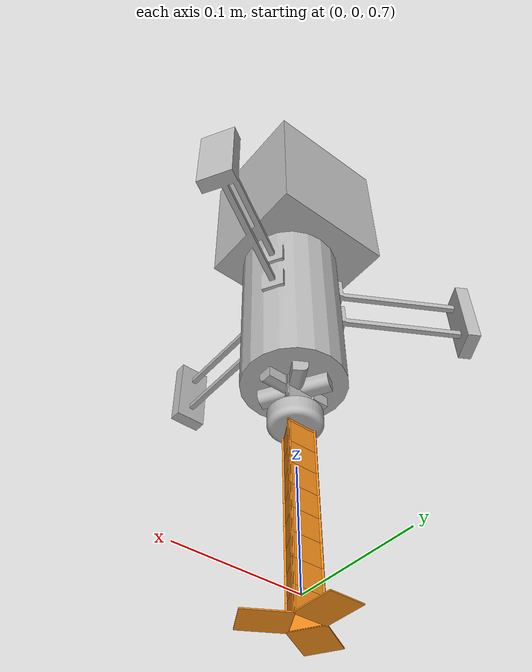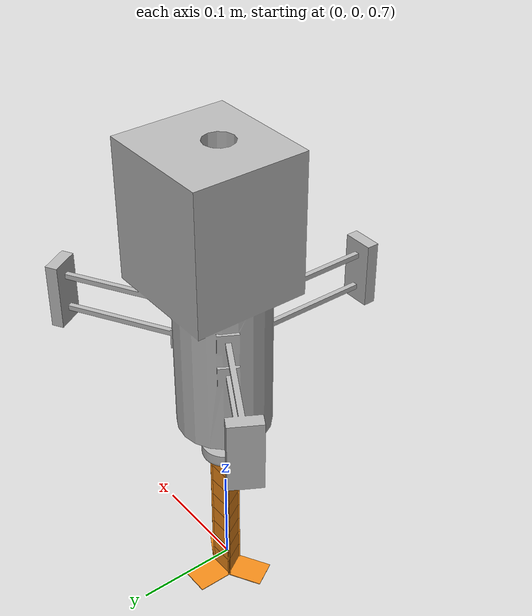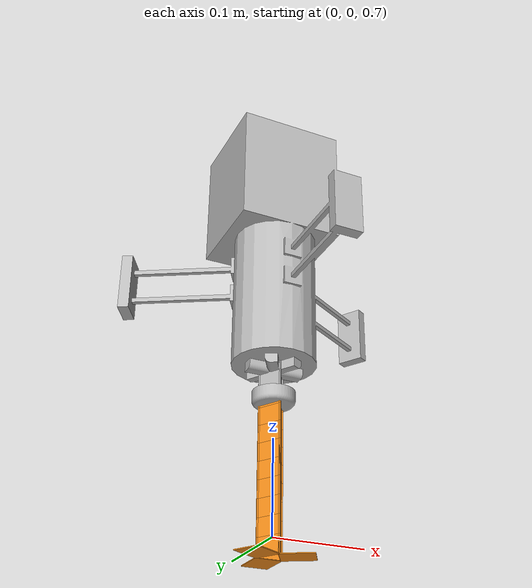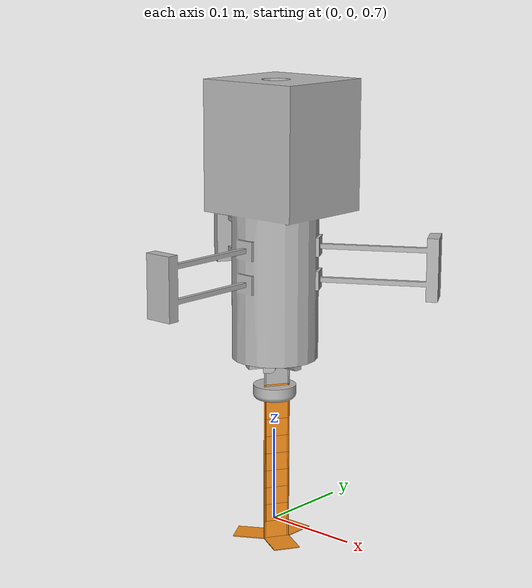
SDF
<sdf version='1.6'>
  <model name='gripper'>
    <link name='gripper_base_link'>
      <pose frame=''>0 0 1 -3.14159 -0 0</pose>
      <inertial>
        <pose frame=''>0 0 0.025 -3.14159 -0 0</pose>
        <mass>1.5</mass>
        <inertia>
          <ixx>0.00995</ixx>
          <ixy>2.73e-06</ixy>
          <ixz>-1.432e-05</ixz>
          <iyy>0.01008</iyy>
          <iyz>0.00012138</iyz>
          <izz>0.00513</izz>
        </inertia>
      </inertial>
      <collision name='gripper_base_link_collision'>
        <pose frame=''>0 0 0 0 -0 0</pose>
        <geometry>
          <mesh>
            <scale>1 1 1</scale>
            <uri>model://gripper_description/meshes/main body collision.STL</uri>
          </mesh>
        </geometry>
      </collision>
      <visual name='gripper_base_link_visual'>
        <pose frame=''>0 0 0 0 -0 0</pose>
        <geometry>
          <mesh>
            <scale>1 1 1</scale>
            <uri>model://gripper_description/meshes/main body visual.STL</uri>
          </mesh>
        </geometry>
      </visual>
    </link>
    <joint name='world_to_base' type='fixed'>
      <child>gripper_base_link</child>
      <parent>world</parent>
    </joint>
    <link name='finger_1_intermediate'>
      <pose frame=''>0 0 1 -3e-06 1.57079 3.14159</pose>
      <inertial>
        <pose frame=''>0 0 0 0 -0 0</pose>
        <mass>0.1</mass>
        <inertia>
          <ixx>5.559e-05</ixx>
          <ixy>-4.723e-05</ixy>
          <ixz>1.16e-06</ixz>
          <iyy>0.00014636</iyy>
          <iyz>1e-06</iyz>
          <izz>0.00015418</izz>
        </inertia>
      </inertial>
      <collision name='finger_1_intermediate_collision'>
        <pose frame=''>0 0 0 0 -0 0</pose>
        <geometry>
          <mesh>
            <scale>1 1 1</scale>
            <uri>model://gripper_description/meshes/nut collision.STL</uri>
          </mesh>
        </geometry>
      </collision>
      <visual name='finger_1_intermediate_visual'>
        <pose frame=''>0 0 0 0 -0 0</pose>
        <geometry>
          <mesh>
            <scale>1 1 1</scale>
            <uri>model://gripper_description/meshes/nut visual.STL</uri>
          </mesh>
        </geometry>
      </visual>
    </link>
    <joint name='finger_1_prismatic_joint' type='prismatic'>
      <child>finger_1_intermediate</child>
      <parent>gripper_base_link</parent>
      <axis>
        <xyz>0 1 0</xyz>
        <limit>
          <lower>0.053</lower>
          <upper>0.141</upper>
          <effort>40</effort>
          <velocity>0.015</velocity>
        </limit>
        <dynamics>
          <damping>1</damping>
          <friction>0</friction>
          <spring_reference>0</spring_reference>
          <spring_stiffness>0</spring_stiffness>
        </dynamics>
        <use_parent_model_frame>0</use_parent_model_frame>
      </axis>
    </joint>
    <link name='finger_1'>
      <pose frame=''>0 0 1 -3e-06 1.57079 3.14159</pose>
      <inertial>
        <pose frame=''>0.007683 -0.000417 0 0 -0 0</pose>
        <mass>0.106333</mass>
        <inertia>
          <ixx>5.62961e-05</ixx>
          <ixy>-4.18516e-05</ixy>
          <ixz>1.16e-06</ixz>
          <iyy>0.000246652</iyy>
          <iyz>1e-06</iyz>
          <izz>0.00025435</izz>
        </inertia>
      </inertial>
      <collision name='finger_1_collision'>
        <pose frame=''>0 0 0 0 -0 0</pose>
        <geometry>
          <mesh>
            <scale>1 1 1</scale>
            <uri>model://gripper_description/meshes/platform only collision.STL</uri>
          </mesh>
        </geometry>
      </collision>
      <collision name='finger_1_segment_link_1_collision_1'>
        <pose frame=''>0.1385 -0.007 0 1.5708 -0 0</pose>
        <geometry>
          <box>
            <size>0.019 0.028 0.0009</size>
          </box>
        </geometry>
      </collision>
      <visual name='finger_1_visual'>
        <pose frame=''>0 0 0 0 -0 0</pose>
        <geometry>
          <mesh>
            <scale>1 1 1</scale>
            <uri>model://gripper_description/meshes/platform only visual.STL</uri>
          </mesh>
        </geometry>
      </visual>
      <visual name='finger_1_segment_link_1_visual_1'>
        <pose frame=''>0.1385 -0.007 0 1.5708 -0 0</pose>
        <geometry>
          <box>
            <size>0.019 0.028 0.0009</size>
          </box>
        </geometry>
      </visual>
      <gravity>1</gravity>
      <velocity_decay/>
    </link>
    <joint name='finger_1_revolute_joint' type='revolute'>
      <child>finger_1</child>
      <parent>finger_1_intermediate</parent>
      <axis>
        <xyz>0 0 1</xyz>
        <limit>
          <lower>-0.7</lower>
          <upper>0.7</upper>
          <effort>40</effort>
          <velocity>0.1</velocity>
        </limit>
        <dynamics>
          <damping>1</damping>
          <friction>0</friction>
          <spring_reference>0</spring_reference>
          <spring_stiffness>0</spring_stiffness>
        </dynamics>
        <use_parent_model_frame>0</use_parent_model_frame>
      </axis>
    </joint>
    <link name='finger_1_segment_link_2'>
      <pose frame=''>-0 0.007 0.852 1.57079 1.57079 3.14159</pose>
      <inertial>
        <pose frame=''>0 0 0 0 -0 0</pose>
        <mass>0.00633333</mass>
        <inertia>
          <ixx>4.14205e-07</ixx>
          <ixy>0</ixy>
          <ixz>0</ixz>
          <iyy>7.62539e-07</iyy>
          <iyz>0</iyz>
          <izz>1.17589e-06</izz>
        </inertia>
      </inertial>
      <collision name='finger_1_segment_link_2_collision'>
        <pose frame=''>0.0095 0 0 0 -0 0</pose>
        <geometry>
          <box>
            <size>0.019 0.028 0.0009</size>
          </box>
        </geometry>
        <surface>
          <contact>
            <ode>
              <max_vel>0</max_vel>
              <min_depth>0.001</min_depth>
            </ode>
          </contact>
          <friction>
            <ode>
              <mu>0.1</mu>
              <mu2>0.1</mu2>
            </ode>
          </friction>
        </surface>
      </collision>
      <visual name='finger_1_segment_link_2_visual'>
        <pose frame=''>0.0095 0 0 0 -0 0</pose>
        <geometry>
          <box>
            <size>0.019 0.028 0.0009</size>
          </box>
        </geometry>
        <material>
          <script>
            <name>Gazebo/Orange</name>
            <uri>file://media/materials/scripts/gazebo.material</uri>
          </script>
        </material>
      </visual>
      <gravity>1</gravity>
      <velocity_decay/>
    </link>
    <joint name='finger_1_segment_joint_1' type='revolute'>
      <child>finger_1_segment_link_2</child>
      <parent>finger_1</parent>
      <axis>
        <xyz>0 1 0</xyz>
        <limit>
          <lower>-1</lower>
          <upper>1</upper>
          <effort>1000</effort>
          <velocity>1</velocity>
        </limit>
        <dynamics>
          <damping>0.001</damping>
          <friction>0</friction>
          <spring_reference>0</spring_reference>
          <spring_stiffness>3</spring_stiffness>
        </dynamics>
        <use_parent_model_frame>0</use_parent_model_frame>
      </axis>
      <physics>
        <provide_feedback>1</provide_feedback>
        <ode>
          <provide_feedback>1</provide_feedback>
          <implicit_spring_damper>1</implicit_spring_damper>
          <cfm_damping>1</cfm_damping>
          <limit>
            <cfm>0</cfm>
            <erp>0.2</erp>
          </limit>
        </ode>
      </physics>
    </joint>
    <link name='finger_1_segment_link_3'>
      <pose frame=''>-0 0.007 0.833 1.57079 1.57079 3.14159</pose>
      <inertial>
        <pose frame=''>0 0 0 0 -0 0</pose>
        <mass>0.00633333</mass>
        <inertia>
          <ixx>4.14205e-07</ixx>
          <ixy>0</ixy>
          <ixz>0</ixz>
          <iyy>7.62539e-07</iyy>
          <iyz>0</iyz>
          <izz>1.17589e-06</izz>
        </inertia>
      </inertial>
      <collision name='finger_1_segment_link_3_collision'>
        <pose frame=''>0.0095 0 0 0 -0 0</pose>
        <geometry>
          <box>
            <size>0.019 0.028 0.0009</size>
          </box>
        </geometry>
        <surface>
          <contact>
            <ode>
              <max_vel>0</max_vel>
              <min_depth>0.001</min_depth>
            </ode>
          </contact>
          <friction>
            <ode>
              <mu>0.1</mu>
              <mu2>0.1</mu2>
            </ode>
          </friction>
        </surface>
      </collision>
      <visual name='finger_1_segment_link_3_visual'>
        <pose frame=''>0.0095 0 0 0 -0 0</pose>
        <geometry>
          <box>
            <size>0.019 0.028 0.0009</size>
          </box>
        </geometry>
        <material>
          <script>
            <name>Gazebo/Orange</name>
            <uri>file://media/materials/scripts/gazebo.material</uri>
          </script>
        </material>
      </visual>
      <gravity>1</gravity>
      <velocity_decay/>
    </link>
    <joint name='finger_1_segment_joint_2' type='revolute'>
      <child>finger_1_segment_link_3</child>
      <parent>finger_1_segment_link_2</parent>
      <axis>
        <xyz>0 1 0</xyz>
        <limit>
          <lower>-1</lower>
          <upper>1</upper>
          <effort>1000</effort>
          <velocity>1</velocity>
        </limit>
        <dynamics>
          <damping>0.001</damping>
          <friction>0</friction>
          <spring_reference>0</spring_reference>
          <spring_stiffness>3</spring_stiffness>
        </dynamics>
        <use_parent_model_frame>0</use_parent_model_frame>
      </axis>
      <physics>
        <provide_feedback>1</provide_feedback>
        <ode>
          <provide_feedback>1</provide_feedback>
          <implicit_spring_damper>1</implicit_spring_damper>
          <cfm_damping>1</cfm_damping>
          <limit>
            <cfm>0</cfm>
            <erp>0.2</erp>
          </limit>
        </ode>
      </physics>
    </joint>
    <link name='finger_1_segment_link_4'>
      <pose frame=''>-0 0.007 0.814 1.57079 1.57079 3.14159</pose>
      <inertial>
        <pose frame=''>0 0 0 0 -0 0</pose>
        <mass>0.00633333</mass>
        <inertia>
          <ixx>4.14205e-07</ixx>
          <ixy>0</ixy>
          <ixz>0</ixz>
          <iyy>7.62539e-07</iyy>
          <iyz>0</iyz>
          <izz>1.17589e-06</izz>
        </inertia>
      </inertial>
      <collision name='finger_1_segment_link_4_collision'>
        <pose frame=''>0.0095 0 0 0 -0 0</pose>
        <geometry>
          <box>
            <size>0.019 0.028 0.0009</size>
          </box>
        </geometry>
        <surface>
          <contact>
            <ode>
              <max_vel>0</max_vel>
              <min_depth>0.001</min_depth>
            </ode>
          </contact>
          <friction>
            <ode>
              <mu>0.1</mu>
              <mu2>0.1</mu2>
            </ode>
          </friction>
        </surface>
      </collision>
      <visual name='finger_1_segment_link_4_visual'>
        <pose frame=''>0.0095 0 0 0 -0 0</pose>
        <geometry>
          <box>
            <size>0.019 0.028 0.0009</size>
          </box>
        </geometry>
        <material>
          <script>
            <name>Gazebo/Orange</name>
            <uri>file://media/materials/scripts/gazebo.material</uri>
          </script>
        </material>
      </visual>
      <gravity>1</gravity>
      <velocity_decay/>
    </link>
    <joint name='finger_1_segment_joint_3' type='revolute'>
      <child>finger_1_segment_link_4</child>
      <parent>finger_1_segment_link_3</parent>
      <axis>
        <xyz>0 1 0</xyz>
        <limit>
          <lower>-1</lower>
          <upper>1</upper>
          <effort>1000</effort>
          <velocity>1</velocity>
        </limit>
        <dynamics>
          <damping>0.001</damping>
          <friction>0</friction>
          <spring_reference>0</spring_reference>
          <spring_stiffness>3</spring_stiffness>
        </dynamics>
        <use_parent_model_frame>0</use_parent_model_frame>
      </axis>
      <physics>
        <provide_feedback>1</provide_feedback>
        <ode>
          <provide_feedback>1</provide_feedback>
          <implicit_spring_damper>1</implicit_spring_damper>
          <cfm_damping>1</cfm_damping>
          <limit>
            <cfm>0</cfm>
            <erp>0.2</erp>
          </limit>
        </ode>
      </physics>
    </joint>
    <link name='finger_1_segment_link_5'>
      <pose frame=''>-0 0.007 0.795 1.57079 1.57079 3.14159</pose>
      <inertial>
        <pose frame=''>0 0 0 0 -0 0</pose>
        <mass>0.00633333</mass>
        <inertia>
          <ixx>4.14205e-07</ixx>
          <ixy>0</ixy>
          <ixz>0</ixz>
          <iyy>7.62539e-07</iyy>
          <iyz>0</iyz>
          <izz>1.17589e-06</izz>
        </inertia>
      </inertial>
      <collision name='finger_1_segment_link_5_collision'>
        <pose frame=''>0.0095 0 0 0 -0 0</pose>
        <geometry>
          <box>
            <size>0.019 0.028 0.0009</size>
          </box>
        </geometry>
        <surface>
          <contact>
            <ode>
              <max_vel>0</max_vel>
              <min_depth>0.001</min_depth>
            </ode>
          </contact>
          <friction>
            <ode>
              <mu>0.1</mu>
              <mu2>0.1</mu2>
            </ode>
          </friction>
        </surface>
      </collision>
      <visual name='finger_1_segment_link_5_visual'>
        <pose frame=''>0.0095 0 0 0 -0 0</pose>
        <geometry>
          <box>
            <size>0.019 0.028 0.0009</size>
          </box>
        </geometry>
        <material>
          <script>
            <name>Gazebo/Orange</name>
            <uri>file://media/materials/scripts/gazebo.material</uri>
          </script>
        </material>
      </visual>
      <gravity>1</gravity>
      <velocity_decay/>
    </link>
    <joint name='finger_1_segment_joint_4' type='revolute'>
      <child>finger_1_segment_link_5</child>
      <parent>finger_1_segment_link_4</parent>
      <axis>
        <xyz>0 1 0</xyz>
        <limit>
          <lower>-1</lower>
          <upper>1</upper>
          <effort>1000</effort>
          <velocity>1</velocity>
        </limit>
        <dynamics>
          <damping>0.001</damping>
          <friction>0</friction>
          <spring_reference>0</spring_reference>
          <spring_stiffness>3</spring_stiffness>
        </dynamics>
        <use_parent_model_frame>0</use_parent_model_frame>
      </axis>
      <physics>
        <provide_feedback>1</provide_feedback>
        <ode>
          <provide_feedback>1</provide_feedback>
          <implicit_spring_damper>1</implicit_spring_damper>
          <cfm_damping>1</cfm_damping>
          <limit>
            <cfm>0</cfm>
            <erp>0.2</erp>
          </limit>
        </ode>
      </physics>
    </joint>
    <link name='finger_1_segment_link_6'>
      <pose frame=''>-0 0.007 0.776 1.57079 1.57079 3.14159</pose>
      <inertial>
        <pose frame=''>0 0 0 0 -0 0</pose>
        <mass>0.00633333</mass>
        <inertia>
          <ixx>4.14205e-07</ixx>
          <ixy>0</ixy>
          <ixz>0</ixz>
          <iyy>7.62539e-07</iyy>
          <iyz>0</iyz>
          <izz>1.17589e-06</izz>
        </inertia>
      </inertial>
      <collision name='finger_1_segment_link_6_collision'>
        <pose frame=''>0.0095 0 0 0 -0 0</pose>
        <geometry>
          <box>
            <size>0.019 0.028 0.0009</size>
          </box>
        </geometry>
        <surface>
          <contact>
            <ode>
              <max_vel>0</max_vel>
              <min_depth>0.001</min_depth>
            </ode>
          </contact>
          <friction>
            <ode>
              <mu>0.1</mu>
              <mu2>0.1</mu2>
            </ode>
          </friction>
        </surface>
      </collision>
      <visual name='finger_1_segment_link_6_visual'>
        <pose frame=''>0.0095 0 0 0 -0 0</pose>
        <geometry>
          <box>
            <size>0.019 0.028 0.0009</size>
          </box>
        </geometry>
        <material>
          <script>
            <name>Gazebo/Orange</name>
            <uri>file://media/materials/scripts/gazebo.material</uri>
          </script>
        </material>
      </visual>
      <gravity>1</gravity>
      <velocity_decay/>
    </link>
    <joint name='finger_1_segment_joint_5' type='revolute'>
      <child>finger_1_segment_link_6</child>
      <parent>finger_1_segment_link_5</parent>
      <axis>
        <xyz>0 1 0</xyz>
        <limit>
          <lower>-1</lower>
          <upper>1</upper>
          <effort>1000</effort>
          <velocity>1</velocity>
        </limit>
        <dynamics>
          <damping>0.001</damping>
          <friction>0</friction>
          <spring_reference>0</spring_reference>
          <spring_stiffness>3</spring_stiffness>
        </dynamics>
        <use_parent_model_frame>0</use_parent_model_frame>
      </axis>
      <physics>
        <provide_feedback>1</provide_feedback>
        <ode>
          <provide_feedback>1</provide_feedback>
          <implicit_spring_damper>1</implicit_spring_damper>
          <cfm_damping>1</cfm_damping>
          <limit>
            <cfm>0</cfm>
            <erp>0.2</erp>
          </limit>
        </ode>
      </physics>
    </joint>
    <link name='finger_1_segment_link_7'>
      <pose frame=''>-0 0.007 0.757 1.57079 1.57079 3.14159</pose>
      <inertial>
        <pose frame=''>0 0 0 0 -0 0</pose>
        <mass>0.00633333</mass>
        <inertia>
          <ixx>4.14205e-07</ixx>
          <ixy>0</ixy>
          <ixz>0</ixz>
          <iyy>7.62539e-07</iyy>
          <iyz>0</iyz>
          <izz>1.17589e-06</izz>
        </inertia>
      </inertial>
      <collision name='finger_1_segment_link_7_collision'>
        <pose frame=''>0.0095 0 0 0 -0 0</pose>
        <geometry>
          <box>
            <size>0.019 0.028 0.0009</size>
          </box>
        </geometry>
        <surface>
          <contact>
            <ode>
              <max_vel>0</max_vel>
              <min_depth>0.001</min_depth>
            </ode>
          </contact>
          <friction>
            <ode>
              <mu>0.1</mu>
              <mu2>0.1</mu2>
            </ode>
          </friction>
        </surface>
      </collision>
      <visual name='finger_1_segment_link_7_visual'>
        <pose frame=''>0.0095 0 0 0 -0 0</pose>
        <geometry>
          <box>
            <size>0.019 0.028 0.0009</size>
          </box>
        </geometry>
        <material>
          <script>
            <name>Gazebo/Orange</name>
            <uri>file://media/materials/scripts/gazebo.material</uri>
          </script>
        </material>
      </visual>
      <gravity>1</gravity>
      <velocity_decay/>
    </link>
    <joint name='finger_1_segment_joint_6' type='revolute'>
      <child>finger_1_segment_link_7</child>
      <parent>finger_1_segment_link_6</parent>
      <axis>
        <xyz>0 1 0</xyz>
        <limit>
          <lower>-1</lower>
          <upper>1</upper>
          <effort>1000</effort>
          <velocity>1</velocity>
        </limit>
        <dynamics>
          <damping>0.001</damping>
          <friction>0</friction>
          <spring_reference>0</spring_reference>
          <spring_stiffness>3</spring_stiffness>
        </dynamics>
        <use_parent_model_frame>0</use_parent_model_frame>
      </axis>
      <physics>
        <provide_feedback>1</provide_feedback>
        <ode>
          <provide_feedback>1</provide_feedback>
          <implicit_spring_damper>1</implicit_spring_damper>
          <cfm_damping>1</cfm_damping>
          <limit>
            <cfm>0</cfm>
            <erp>0.2</erp>
          </limit>
        </ode>
      </physics>
    </joint>
    <link name='finger_1_segment_link_8'>
      <pose frame=''>-0 0.007 0.738 1.57079 1.57079 3.14159</pose>
      <inertial>
        <pose frame=''>0 0 0 0 -0 0</pose>
        <mass>0.00633333</mass>
        <inertia>
          <ixx>4.14205e-07</ixx>
          <ixy>0</ixy>
          <ixz>0</ixz>
          <iyy>7.62539e-07</iyy>
          <iyz>0</iyz>
          <izz>1.17589e-06</izz>
        </inertia>
      </inertial>
      <collision name='finger_1_segment_link_8_collision'>
        <pose frame=''>0.0095 0 0 0 -0 0</pose>
        <geometry>
          <box>
            <size>0.019 0.028 0.0009</size>
          </box>
        </geometry>
        <surface>
          <contact>
            <ode>
              <max_vel>0</max_vel>
              <min_depth>0.001</min_depth>
            </ode>
          </contact>
          <friction>
            <ode>
              <mu>0.1</mu>
              <mu2>0.1</mu2>
            </ode>
          </friction>
        </surface>
      </collision>
      <visual name='finger_1_segment_link_8_visual'>
        <pose frame=''>0.0095 0 0 0 -0 0</pose>
        <geometry>
          <box>
            <size>0.019 0.028 0.0009</size>
          </box>
        </geometry>
        <material>
          <script>
            <name>Gazebo/Orange</name>
            <uri>file://media/materials/scripts/gazebo.material</uri>
          </script>
        </material>
      </visual>
      <gravity>1</gravity>
      <velocity_decay/>
    </link>
    <joint name='finger_1_segment_joint_7' type='revolute'>
      <child>finger_1_segment_link_8</child>
      <parent>finger_1_segment_link_7</parent>
      <axis>
        <xyz>0 1 0</xyz>
        <limit>
          <lower>-1</lower>
          <upper>1</upper>
          <effort>1000</effort>
          <velocity>1</velocity>
        </limit>
        <dynamics>
          <damping>0.001</damping>
          <friction>0</friction>
          <spring_reference>0</spring_reference>
          <spring_stiffness>3</spring_stiffness>
        </dynamics>
        <use_parent_model_frame>0</use_parent_model_frame>
      </axis>
      <physics>
        <provide_feedback>1</provide_feedback>
        <ode>
          <provide_feedback>1</provide_feedback>
          <implicit_spring_damper>1</implicit_spring_damper>
          <cfm_damping>1</cfm_damping>
          <limit>
            <cfm>0</cfm>
            <erp>0.2</erp>
          </limit>
        </ode>
      </physics>
    </joint>
    <link name='finger_1_segment_link_9'>
      <pose frame=''>-0 0.007 0.719 1.57079 1.57079 3.14159</pose>
      <inertial>
        <pose frame=''>0 0 0 0 -0 0</pose>
        <mass>0.00633333</mass>
        <inertia>
          <ixx>4.14205e-07</ixx>
          <ixy>0</ixy>
          <ixz>0</ixz>
          <iyy>7.62539e-07</iyy>
          <iyz>0</iyz>
          <izz>1.17589e-06</izz>
        </inertia>
      </inertial>
      <collision name='finger_1_segment_link_9_collision'>
        <pose frame=''>0.0095 0 0 0 -0 0</pose>
        <geometry>
          <box>
            <size>0.019 0.028 0.0009</size>
          </box>
        </geometry>
        <surface>
          <contact>
            <ode>
              <max_vel>0</max_vel>
              <min_depth>0.001</min_depth>
            </ode>
          </contact>
          <friction>
            <ode>
              <mu>0.1</mu>
              <mu2>0.1</mu2>
            </ode>
          </friction>
        </surface>
      </collision>
      <visual name='finger_1_segment_link_9_visual'>
        <pose frame=''>0.0095 0 0 0 -0 0</pose>
        <geometry>
          <box>
            <size>0.019 0.028 0.0009</size>
          </box>
        </geometry>
        <material>
          <script>
            <name>Gazebo/Orange</name>
            <uri>file://media/materials/scripts/gazebo.material</uri>
          </script>
        </material>
      </visual>
      <gravity>1</gravity>
      <velocity_decay/>
    </link>
    <joint name='finger_1_segment_joint_8' type='revolute'>
      <child>finger_1_segment_link_9</child>
      <parent>finger_1_segment_link_8</parent>
      <axis>
        <xyz>0 1 0</xyz>
        <limit>
          <lower>-1</lower>
          <upper>1</upper>
          <effort>1000</effort>
          <velocity>1</velocity>
        </limit>
        <dynamics>
          <damping>0.001</damping>
          <friction>0</friction>
          <spring_reference>0</spring_reference>
          <spring_stiffness>3</spring_stiffness>
        </dynamics>
        <use_parent_model_frame>0</use_parent_model_frame>
      </axis>
      <physics>
        <provide_feedback>1</provide_feedback>
        <ode>
          <provide_feedback>1</provide_feedback>
          <implicit_spring_damper>1</implicit_spring_damper>
          <cfm_damping>1</cfm_damping>
          <limit>
            <cfm>0</cfm>
            <erp>0.2</erp>
          </limit>
        </ode>
      </physics>
    </joint>
    <link name='finger_1_segment_link_10'>
      <pose frame=''>-0 0.007 0.7 1.57079 1.57079 3.14159</pose>
      <inertial>
        <pose frame=''>0.0095 0 0 0 -0 0</pose>
        <mass>0.0126667</mass>
        <inertia>
          <ixx>1.59009e-06</ixx>
          <ixy>0</ixy>
          <ixz>-4.66397e-23</ixz>
          <iyy>2.66824e-06</iyy>
          <iyz>0</iyz>
          <izz>2.73326e-06</izz>
        </inertia>
      </inertial>
      <collision name='finger_1_segment_link_10_collision'>
        <pose frame=''>0.0095 0 0 0 -0 0</pose>
        <geometry>
          <box>
            <size>0.019 0.028 0.0009</size>
          </box>
        </geometry>
        <surface>
          <contact>
            <ode>
              <max_vel>0</max_vel>
              <min_depth>0.001</min_depth>
            </ode>
          </contact>
          <friction>
            <ode>
              <mu>0.1</mu>
              <mu2>0.1</mu2>
            </ode>
          </friction>
        </surface>
      </collision>
      <collision name='finger_1_segment_link_10_fixed_joint_lump__finger_1_finger_hook_link_collision_1'>
        <pose frame=''>0.019 0 0.0175 3.14159 -1.57079 3.14159</pose>
        <geometry>
          <box>
            <size>0.035 0.028 0.0009</size>
          </box>
        </geometry>
        <surface>
          <contact>
            <ode>
              <max_vel>0</max_vel>
              <min_depth>0.001</min_depth>
            </ode>
          </contact>
          <friction>
            <ode>
              <mu>0.1</mu>
              <mu2>0.1</mu2>
            </ode>
          </friction>
        </surface>
      </collision>
      <visual name='finger_1_segment_link_10_visual'>
        <pose frame=''>0.0095 0 0 0 -0 0</pose>
        <geometry>
          <box>
            <size>0.019 0.028 0.0009</size>
          </box>
        </geometry>
        <material>
          <script>
            <name>Gazebo/Orange</name>
            <uri>file://media/materials/scripts/gazebo.material</uri>
          </script>
        </material>
      </visual>
      <visual name='finger_1_segment_link_10_fixed_joint_lump__finger_1_finger_hook_link_visual_1'>
        <pose frame=''>0.019 0 0.0175 3.14159 -1.57079 3.14159</pose>
        <geometry>
          <box>
            <size>0.035 0.028 0.0009</size>
          </box>
        </geometry>
        <material>
          <script>
            <name>Gazebo/Orange</name>
            <uri>file://media/materials/scripts/gazebo.material</uri>
          </script>
        </material>
      </visual>
      <velocity_decay/>
      <gravity>1</gravity>
      <velocity_decay/>
    </link>
    <joint name='finger_1_segment_joint_9' type='revolute'>
      <child>finger_1_segment_link_10</child>
      <parent>finger_1_segment_link_9</parent>
      <axis>
        <xyz>0 1 0</xyz>
        <limit>
          <lower>-1</lower>
          <upper>1</upper>
          <effort>1000</effort>
          <velocity>1</velocity>
        </limit>
        <dynamics>
          <damping>0.001</damping>
          <friction>0</friction>
          <spring_reference>0</spring_reference>
          <spring_stiffness>3</spring_stiffness>
        </dynamics>
        <use_parent_model_frame>0</use_parent_model_frame>
      </axis>
      <physics>
        <provide_feedback>1</provide_feedback>
        <ode>
          <provide_feedback>1</provide_feedback>
          <implicit_spring_damper>1</implicit_spring_damper>
          <cfm_damping>1</cfm_damping>
          <limit>
            <cfm>0</cfm>
            <erp>0.2</erp>
          </limit>
        </ode>
      </physics>
    </joint>
    <link name='finger_2_intermediate'>
      <pose frame=''>0 0 1 -2.09439 1.57079 3.14159</pose>
      <inertial>
        <pose frame=''>0 0 0 0 -0 0</pose>
        <mass>0.1</mass>
        <inertia>
          <ixx>5.559e-05</ixx>
          <ixy>-4.723e-05</ixy>
          <ixz>1.16e-06</ixz>
          <iyy>0.00014636</iyy>
          <iyz>1e-06</iyz>
          <izz>0.00015418</izz>
        </inertia>
      </inertial>
      <collision name='finger_2_intermediate_collision'>
        <pose frame=''>0 0 0 0 -0 0</pose>
        <geometry>
          <mesh>
            <scale>1 1 1</scale>
            <uri>model://gripper_description/meshes/nut collision.STL</uri>
          </mesh>
        </geometry>
      </collision>
      <visual name='finger_2_intermediate_visual'>
        <pose frame=''>0 0 0 0 -0 0</pose>
        <geometry>
          <mesh>
            <scale>1 1 1</scale>
            <uri>model://gripper_description/meshes/nut visual.STL</uri>
          </mesh>
        </geometry>
      </visual>
    </link>
    <joint name='finger_2_prismatic_joint' type='prismatic'>
      <child>finger_2_intermediate</child>
      <parent>gripper_base_link</parent>
      <axis>
        <xyz>0 1 0</xyz>
        <limit>
          <lower>0.053</lower>
          <upper>0.141</upper>
          <effort>40</effort>
          <velocity>0.015</velocity>
        </limit>
        <dynamics>
          <damping>1</damping>
          <friction>0</friction>
          <spring_reference>0</spring_reference>
          <spring_stiffness>0</spring_stiffness>
        </dynamics>
        <use_parent_model_frame>0</use_parent_model_frame>
      </axis>
    </joint>
    <link name='finger_2'>
      <pose frame=''>0 0 1 -2.09439 1.57079 3.14159</pose>
      <inertial>
        <pose frame=''>0.007683 -0.000417 0 0 -0 0</pose>
        <mass>0.106333</mass>
        <inertia>
          <ixx>5.62961e-05</ixx>
          <ixy>-4.18516e-05</ixy>
          <ixz>1.16e-06</ixz>
          <iyy>0.000246652</iyy>
          <iyz>1e-06</iyz>
          <izz>0.00025435</izz>
        </inertia>
      </inertial>
      <collision name='finger_2_collision'>
        <pose frame=''>0 0 0 0 -0 0</pose>
        <geometry>
          <mesh>
            <scale>1 1 1</scale>
            <uri>model://gripper_description/meshes/platform only collision.STL</uri>
          </mesh>
        </geometry>
      </collision>
      <collision name='finger_2_segment_link_1_collision_1'>
        <pose frame=''>0.1385 -0.007 0 1.5708 -0 0</pose>
        <geometry>
          <box>
            <size>0.019 0.028 0.0009</size>
          </box>
        </geometry>
      </collision>
      <visual name='finger_2_visual'>
        <pose frame=''>0 0 0 0 -0 0</pose>
        <geometry>
          <mesh>
            <scale>1 1 1</scale>
            <uri>model://gripper_description/meshes/platform only visual.STL</uri>
          </mesh>
        </geometry>
      </visual>
      <visual name='finger_2_segment_link_1_visual_1'>
        <pose frame=''>0.1385 -0.007 0 1.5708 -0 0</pose>
        <geometry>
          <box>
            <size>0.019 0.028 0.0009</size>
          </box>
        </geometry>
      </visual>
      <gravity>1</gravity>
      <velocity_decay/>
    </link>
    <joint name='finger_2_revolute_joint' type='revolute'>
      <child>finger_2</child>
      <parent>finger_2_intermediate</parent>
      <axis>
        <xyz>0 0 1</xyz>
        <limit>
          <lower>-0.7</lower>
          <upper>0.7</upper>
          <effort>40</effort>
          <velocity>0.1</velocity>
        </limit>
        <dynamics>
          <damping>1</damping>
          <friction>0</friction>
          <spring_reference>0</spring_reference>
          <spring_stiffness>0</spring_stiffness>
        </dynamics>
        <use_parent_model_frame>0</use_parent_model_frame>
      </axis>
    </joint>
    <link name='finger_2_segment_link_2'>
      <pose frame=''>-0.006062 -0.0035 0.852 -0.523603 1.57079 3.14159</pose>
      <inertial>
        <pose frame=''>0 0 0 0 -0 0</pose>
        <mass>0.00633333</mass>
        <inertia>
          <ixx>4.14205e-07</ixx>
          <ixy>0</ixy>
          <ixz>0</ixz>
          <iyy>7.62539e-07</iyy>
          <iyz>0</iyz>
          <izz>1.17589e-06</izz>
        </inertia>
      </inertial>
      <collision name='finger_2_segment_link_2_collision'>
        <pose frame=''>0.0095 0 0 0 -0 0</pose>
        <geometry>
          <box>
            <size>0.019 0.028 0.0009</size>
          </box>
        </geometry>
        <surface>
          <contact>
            <ode>
              <max_vel>0</max_vel>
              <min_depth>0.001</min_depth>
            </ode>
          </contact>
          <friction>
            <ode>
              <mu>0.1</mu>
              <mu2>0.1</mu2>
            </ode>
          </friction>
        </surface>
      </collision>
      <visual name='finger_2_segment_link_2_visual'>
        <pose frame=''>0.0095 0 0 0 -0 0</pose>
        <geometry>
          <box>
            <size>0.019 0.028 0.0009</size>
          </box>
        </geometry>
        <material>
          <script>
            <name>Gazebo/Orange</name>
            <uri>file://media/materials/scripts/gazebo.material</uri>
          </script>
        </material>
      </visual>
      <gravity>1</gravity>
      <velocity_decay/>
    </link>
    <joint name='finger_2_segment_joint_1' type='revolute'>
      <child>finger_2_segment_link_2</child>
      <parent>finger_2</parent>
      <axis>
        <xyz>0 1 0</xyz>
        <limit>
          <lower>-1</lower>
          <upper>1</upper>
          <effort>1000</effort>
          <velocity>1</velocity>
        </limit>
        <dynamics>
          <damping>0.001</damping>
          <friction>0</friction>
          <spring_reference>0</spring_reference>
          <spring_stiffness>3</spring_stiffness>
        </dynamics>
        <use_parent_model_frame>0</use_parent_model_frame>
      </axis>
      <physics>
        <provide_feedback>1</provide_feedback>
        <ode>
          <provide_feedback>1</provide_feedback>
          <implicit_spring_damper>1</implicit_spring_damper>
          <cfm_damping>1</cfm_damping>
          <limit>
            <cfm>0</cfm>
            <erp>0.2</erp>
          </limit>
        </ode>
      </physics>
    </joint>
    <link name='finger_2_segment_link_3'>
      <pose frame=''>-0.006062 -0.0035 0.833 -0.523603 1.57079 3.14159</pose>
      <inertial>
        <pose frame=''>0 0 0 0 -0 0</pose>
        <mass>0.00633333</mass>
        <inertia>
          <ixx>4.14205e-07</ixx>
          <ixy>0</ixy>
          <ixz>0</ixz>
          <iyy>7.62539e-07</iyy>
          <iyz>0</iyz>
          <izz>1.17589e-06</izz>
        </inertia>
      </inertial>
      <collision name='finger_2_segment_link_3_collision'>
        <pose frame=''>0.0095 0 0 0 -0 0</pose>
        <geometry>
          <box>
            <size>0.019 0.028 0.0009</size>
          </box>
        </geometry>
        <surface>
          <contact>
            <ode>
              <max_vel>0</max_vel>
              <min_depth>0.001</min_depth>
            </ode>
          </contact>
          <friction>
            <ode>
              <mu>0.1</mu>
              <mu2>0.1</mu2>
            </ode>
          </friction>
        </surface>
      </collision>
      <visual name='finger_2_segment_link_3_visual'>
        <pose frame=''>0.0095 0 0 0 -0 0</pose>
        <geometry>
          <box>
            <size>0.019 0.028 0.0009</size>
          </box>
        </geometry>
        <material>
          <script>
            <name>Gazebo/Orange</name>
            <uri>file://media/materials/scripts/gazebo.material</uri>
          </script>
        </material>
      </visual>
      <gravity>1</gravity>
      <velocity_decay/>
    </link>
    <joint name='finger_2_segment_joint_2' type='revolute'>
      <child>finger_2_segment_link_3</child>
      <parent>finger_2_segment_link_2</parent>
      <axis>
        <xyz>0 1 0</xyz>
        <limit>
          <lower>-1</lower>
          <upper>1</upper>
          <effort>1000</effort>
          <velocity>1</velocity>
        </limit>
        <dynamics>
          <damping>0.001</damping>
          <friction>0</friction>
          <spring_reference>0</spring_reference>
          <spring_stiffness>3</spring_stiffness>
        </dynamics>
        <use_parent_model_frame>0</use_parent_model_frame>
      </axis>
      <physics>
        <provide_feedback>1</provide_feedback>
        <ode>
          <provide_feedback>1</provide_feedback>
          <implicit_spring_damper>1</implicit_spring_damper>
          <cfm_damping>1</cfm_damping>
          <limit>
            <cfm>0</cfm>
            <erp>0.2</erp>
          </limit>
        </ode>
      </physics>
    </joint>
    <link name='finger_2_segment_link_4'>
      <pose frame=''>-0.006062 -0.0035 0.814 -0.523603 1.57079 3.14159</pose>
      <inertial>
        <pose frame=''>0 0 0 0 -0 0</pose>
        <mass>0.00633333</mass>
        <inertia>
          <ixx>4.14205e-07</ixx>
          <ixy>0</ixy>
          <ixz>0</ixz>
          <iyy>7.62539e-07</iyy>
          <iyz>0</iyz>
          <izz>1.17589e-06</izz>
        </inertia>
      </inertial>
      <collision name='finger_2_segment_link_4_collision'>
        <pose frame=''>0.0095 0 0 0 -0 0</pose>
        <geometry>
          <box>
            <size>0.019 0.028 0.0009</size>
          </box>
        </geometry>
        <surface>
          <contact>
            <ode>
              <max_vel>0</max_vel>
              <min_depth>0.001</min_depth>
            </ode>
          </contact>
          <friction>
            <ode>
              <mu>0.1</mu>
              <mu2>0.1</mu2>
            </ode>
          </friction>
        </surface>
      </collision>
      <visual name='finger_2_segment_link_4_visual'>
        <pose frame=''>0.0095 0 0 0 -0 0</pose>
        <geometry>
          <box>
            <size>0.019 0.028 0.0009</size>
          </box>
        </geometry>
        <material>
          <script>
            <name>Gazebo/Orange</name>
            <uri>file://media/materials/scripts/gazebo.material</uri>
          </script>
        </material>
      </visual>
      <gravity>1</gravity>
      <velocity_decay/>
    </link>
    <joint name='finger_2_segment_joint_3' type='revolute'>
      <child>finger_2_segment_link_4</child>
      <parent>finger_2_segment_link_3</parent>
      <axis>
        <xyz>0 1 0</xyz>
        <limit>
          <lower>-1</lower>
          <upper>1</upper>
          <effort>1000</effort>
          <velocity>1</velocity>
        </limit>
        <dynamics>
          <damping>0.001</damping>
          <friction>0</friction>
          <spring_reference>0</spring_reference>
          <spring_stiffness>3</spring_stiffness>
        </dynamics>
        <use_parent_model_frame>0</use_parent_model_frame>
      </axis>
      <physics>
        <provide_feedback>1</provide_feedback>
        <ode>
          <provide_feedback>1</provide_feedback>
          <implicit_spring_damper>1</implicit_spring_damper>
          <cfm_damping>1</cfm_damping>
          <limit>
            <cfm>0</cfm>
            <erp>0.2</erp>
          </limit>
        </ode>
      </physics>
    </joint>
    <link name='finger_2_segment_link_5'>
      <pose frame=''>-0.006062 -0.0035 0.795 -0.523603 1.57079 3.14159</pose>
      <inertial>
        <pose frame=''>0 0 0 0 -0 0</pose>
        <mass>0.00633333</mass>
        <inertia>
          <ixx>4.14205e-07</ixx>
          <ixy>0</ixy>
          <ixz>0</ixz>
          <iyy>7.62539e-07</iyy>
          <iyz>0</iyz>
          <izz>1.17589e-06</izz>
        </inertia>
      </inertial>
      <collision name='finger_2_segment_link_5_collision'>
        <pose frame=''>0.0095 0 0 0 -0 0</pose>
        <geometry>
          <box>
            <size>0.019 0.028 0.0009</size>
          </box>
        </geometry>
        <surface>
          <contact>
            <ode>
              <max_vel>0</max_vel>
              <min_depth>0.001</min_depth>
            </ode>
          </contact>
          <friction>
            <ode>
              <mu>0.1</mu>
              <mu2>0.1</mu2>
            </ode>
          </friction>
        </surface>
      </collision>
      <visual name='finger_2_segment_link_5_visual'>
        <pose frame=''>0.0095 0 0 0 -0 0</pose>
        <geometry>
          <box>
            <size>0.019 0.028 0.0009</size>
          </box>
        </geometry>
        <material>
          <script>
            <name>Gazebo/Orange</name>
            <uri>file://media/materials/scripts/gazebo.material</uri>
          </script>
        </material>
      </visual>
      <gravity>1</gravity>
      <velocity_decay/>
    </link>
    <joint name='finger_2_segment_joint_4' type='revolute'>
      <child>finger_2_segment_link_5</child>
      <parent>finger_2_segment_link_4</parent>
      <axis>
        <xyz>0 1 0</xyz>
        <limit>
          <lower>-1</lower>
          <upper>1</upper>
          <effort>1000</effort>
          <velocity>1</velocity>
        </limit>
        <dynamics>
          <damping>0.001</damping>
          <friction>0</friction>
          <spring_reference>0</spring_reference>
          <spring_stiffness>3</spring_stiffness>
        </dynamics>
        <use_parent_model_frame>0</use_parent_model_frame>
      </axis>
      <physics>
        <provide_feedback>1</provide_feedback>
        <ode>
          <provide_feedback>1</provide_feedback>
          <implicit_spring_damper>1</implicit_spring_damper>
          <cfm_damping>1</cfm_damping>
          <limit>
            <cfm>0</cfm>
            <erp>0.2</erp>
          </limit>
        </ode>
      </physics>
    </joint>
    <link name='finger_2_segment_link_6'>
      <pose frame=''>-0.006062 -0.0035 0.776 -0.523603 1.57079 3.14159</pose>
      <inertial>
        <pose frame=''>0 0 0 0 -0 0</pose>
        <mass>0.00633333</mass>
        <inertia>
          <ixx>4.14205e-07</ixx>
          <ixy>0</ixy>
          <ixz>0</ixz>
          <iyy>7.62539e-07</iyy>
          <iyz>0</iyz>
          <izz>1.17589e-06</izz>
        </inertia>
      </inertial>
      <collision name='finger_2_segment_link_6_collision'>
        <pose frame=''>0.0095 0 0 0 -0 0</pose>
        <geometry>
          <box>
            <size>0.019 0.028 0.0009</size>
          </box>
        </geometry>
        <surface>
          <contact>
            <ode>
              <max_vel>0</max_vel>
              <min_depth>0.001</min_depth>
            </ode>
          </contact>
          <friction>
            <ode>
              <mu>0.1</mu>
              <mu2>0.1</mu2>
            </ode>
          </friction>
        </surface>
      </collision>
      <visual name='finger_2_segment_link_6_visual'>
        <pose frame=''>0.0095 0 0 0 -0 0</pose>
        <geometry>
          <box>
            <size>0.019 0.028 0.0009</size>
          </box>
        </geometry>
        <material>
          <script>
            <name>Gazebo/Orange</name>
            <uri>file://media/materials/scripts/gazebo.material</uri>
          </script>
        </material>
      </visual>
      <gravity>1</gravity>
      <velocity_decay/>
    </link>
    <joint name='finger_2_segment_joint_5' type='revolute'>
      <child>finger_2_segment_link_6</child>
      <parent>finger_2_segment_link_5</parent>
      <axis>
        <xyz>0 1 0</xyz>
        <limit>
          <lower>-1</lower>
          <upper>1</upper>
          <effort>1000</effort>
          <velocity>1</velocity>
        </limit>
        <dynamics>
          <damping>0.001</damping>
          <friction>0</friction>
          <spring_reference>0</spring_reference>
          <spring_stiffness>3</spring_stiffness>
        </dynamics>
        <use_parent_model_frame>0</use_parent_model_frame>
      </axis>
      <physics>
        <provide_feedback>1</provide_feedback>
        <ode>
          <provide_feedback>1</provide_feedback>
          <implicit_spring_damper>1</implicit_spring_damper>
          <cfm_damping>1</cfm_damping>
          <limit>
            <cfm>0</cfm>
            <erp>0.2</erp>
          </limit>
        </ode>
      </physics>
    </joint>
    <link name='finger_2_segment_link_7'>
      <pose frame=''>-0.006062 -0.0035 0.757 -0.523603 1.57079 3.14159</pose>
      <inertial>
        <pose frame=''>0 0 0 0 -0 0</pose>
        <mass>0.00633333</mass>
        <inertia>
          <ixx>4.14205e-07</ixx>
          <ixy>0</ixy>
          <ixz>0</ixz>
          <iyy>7.62539e-07</iyy>
          <iyz>0</iyz>
          <izz>1.17589e-06</izz>
        </inertia>
      </inertial>
      <collision name='finger_2_segment_link_7_collision'>
        <pose frame=''>0.0095 0 0 0 -0 0</pose>
        <geometry>
          <box>
            <size>0.019 0.028 0.0009</size>
          </box>
        </geometry>
        <surface>
          <contact>
            <ode>
              <max_vel>0</max_vel>
              <min_depth>0.001</min_depth>
            </ode>
          </contact>
          <friction>
            <ode>
              <mu>0.1</mu>
              <mu2>0.1</mu2>
            </ode>
          </friction>
        </surface>
      </collision>
      <visual name='finger_2_segment_link_7_visual'>
        <pose frame=''>0.0095 0 0 0 -0 0</pose>
        <geometry>
          <box>
            <size>0.019 0.028 0.0009</size>
          </box>
        </geometry>
        <material>
          <script>
            <name>Gazebo/Orange</name>
            <uri>file://media/materials/scripts/gazebo.material</uri>
          </script>
        </material>
      </visual>
      <gravity>1</gravity>
      <velocity_decay/>
    </link>
    <joint name='finger_2_segment_joint_6' type='revolute'>
      <child>finger_2_segment_link_7</child>
      <parent>finger_2_segment_link_6</parent>
      <axis>
        <xyz>0 1 0</xyz>
        <limit>
          <lower>-1</lower>
          <upper>1</upper>
          <effort>1000</effort>
          <velocity>1</velocity>
        </limit>
        <dynamics>
          <damping>0.001</damping>
          <friction>0</friction>
          <spring_reference>0</spring_reference>
          <spring_stiffness>3</spring_stiffness>
        </dynamics>
        <use_parent_model_frame>0</use_parent_model_frame>
      </axis>
      <physics>
        <provide_feedback>1</provide_feedback>
        <ode>
          <provide_feedback>1</provide_feedback>
          <implicit_spring_damper>1</implicit_spring_damper>
          <cfm_damping>1</cfm_damping>
          <limit>
            <cfm>0</cfm>
            <erp>0.2</erp>
          </limit>
        </ode>
      </physics>
    </joint>
    <link name='finger_2_segment_link_8'>
      <pose frame=''>-0.006062 -0.0035 0.738 -0.523603 1.57079 3.14159</pose>
      <inertial>
        <pose frame=''>0 0 0 0 -0 0</pose>
        <mass>0.00633333</mass>
        <inertia>
          <ixx>4.14205e-07</ixx>
          <ixy>0</ixy>
          <ixz>0</ixz>
          <iyy>7.62539e-07</iyy>
          <iyz>0</iyz>
          <izz>1.17589e-06</izz>
        </inertia>
      </inertial>
      <collision name='finger_2_segment_link_8_collision'>
        <pose frame=''>0.0095 0 0 0 -0 0</pose>
        <geometry>
          <box>
            <size>0.019 0.028 0.0009</size>
          </box>
        </geometry>
        <surface>
          <contact>
            <ode>
              <max_vel>0</max_vel>
              <min_depth>0.001</min_depth>
            </ode>
          </contact>
          <friction>
            <ode>
              <mu>0.1</mu>
              <mu2>0.1</mu2>
            </ode>
          </friction>
        </surface>
      </collision>
      <visual name='finger_2_segment_link_8_visual'>
        <pose frame=''>0.0095 0 0 0 -0 0</pose>
        <geometry>
          <box>
            <size>0.019 0.028 0.0009</size>
          </box>
        </geometry>
        <material>
          <script>
            <name>Gazebo/Orange</name>
            <uri>file://media/materials/scripts/gazebo.material</uri>
          </script>
        </material>
      </visual>
      <gravity>1</gravity>
      <velocity_decay/>
    </link>
    <joint name='finger_2_segment_joint_7' type='revolute'>
      <child>finger_2_segment_link_8</child>
      <parent>finger_2_segment_link_7</parent>
      <axis>
        <xyz>0 1 0</xyz>
        <limit>
          <lower>-1</lower>
          <upper>1</upper>
          <effort>1000</effort>
          <velocity>1</velocity>
        </limit>
        <dynamics>
          <damping>0.001</damping>
          <friction>0</friction>
          <spring_reference>0</spring_reference>
          <spring_stiffness>3</spring_stiffness>
        </dynamics>
        <use_parent_model_frame>0</use_parent_model_frame>
      </axis>
      <physics>
        <provide_feedback>1</provide_feedback>
        <ode>
          <provide_feedback>1</provide_feedback>
          <implicit_spring_damper>1</implicit_spring_damper>
          <cfm_damping>1</cfm_damping>
          <limit>
            <cfm>0</cfm>
            <erp>0.2</erp>
          </limit>
        </ode>
      </physics>
    </joint>
    <link name='finger_2_segment_link_9'>
      <pose frame=''>-0.006062 -0.0035 0.719 -0.523603 1.57079 3.14159</pose>
      <inertial>
        <pose frame=''>0 0 0 0 -0 0</pose>
        <mass>0.00633333</mass>
        <inertia>
          <ixx>4.14205e-07</ixx>
          <ixy>0</ixy>
          <ixz>0</ixz>
          <iyy>7.62539e-07</iyy>
          <iyz>0</iyz>
          <izz>1.17589e-06</izz>
        </inertia>
      </inertial>
      <collision name='finger_2_segment_link_9_collision'>
        <pose frame=''>0.0095 0 0 0 -0 0</pose>
        <geometry>
          <box>
            <size>0.019 0.028 0.0009</size>
          </box>
        </geometry>
        <surface>
          <contact>
            <ode>
              <max_vel>0</max_vel>
              <min_depth>0.001</min_depth>
            </ode>
          </contact>
          <friction>
            <ode>
              <mu>0.1</mu>
              <mu2>0.1</mu2>
            </ode>
          </friction>
        </surface>
      </collision>
      <visual name='finger_2_segment_link_9_visual'>
        <pose frame=''>0.0095 0 0 0 -0 0</pose>
        <geometry>
          <box>
            <size>0.019 0.028 0.0009</size>
          </box>
        </geometry>
        <material>
          <script>
            <name>Gazebo/Orange</name>
            <uri>file://media/materials/scripts/gazebo.material</uri>
          </script>
        </material>
      </visual>
      <gravity>1</gravity>
      <velocity_decay/>
    </link>
    <joint name='finger_2_segment_joint_8' type='revolute'>
      <child>finger_2_segment_link_9</child>
      <parent>finger_2_segment_link_8</parent>
      <axis>
        <xyz>0 1 0</xyz>
        <limit>
          <lower>-1</lower>
          <upper>1</upper>
          <effort>1000</effort>
          <velocity>1</velocity>
        </limit>
        <dynamics>
          <damping>0.001</damping>
          <friction>0</friction>
          <spring_reference>0</spring_reference>
          <spring_stiffness>3</spring_stiffness>
        </dynamics>
        <use_parent_model_frame>0</use_parent_model_frame>
      </axis>
      <physics>
        <provide_feedback>1</provide_feedback>
        <ode>
          <provide_feedback>1</provide_feedback>
          <implicit_spring_damper>1</implicit_spring_damper>
          <cfm_damping>1</cfm_damping>
          <limit>
            <cfm>0</cfm>
            <erp>0.2</erp>
          </limit>
        </ode>
      </physics>
    </joint>
    <link name='finger_2_segment_link_10'>
      <pose frame=''>-0.006062 -0.0035 0.7 -0.523603 1.57079 3.14159</pose>
      <inertial>
        <pose frame=''>0.0095 0 0 0 -0 0</pose>
        <mass>0.0126667</mass>
        <inertia>
          <ixx>1.59009e-06</ixx>
          <ixy>0</ixy>
          <ixz>-4.66397e-23</ixz>
          <iyy>2.66824e-06</iyy>
          <iyz>0</iyz>
          <izz>2.73326e-06</izz>
        </inertia>
      </inertial>
      <collision name='finger_2_segment_link_10_collision'>
        <pose frame=''>0.0095 0 0 0 -0 0</pose>
        <geometry>
          <box>
            <size>0.019 0.028 0.0009</size>
          </box>
        </geometry>
        <surface>
          <contact>
            <ode>
              <max_vel>0</max_vel>
              <min_depth>0.001</min_depth>
            </ode>
          </contact>
          <friction>
            <ode>
              <mu>0.1</mu>
              <mu2>0.1</mu2>
            </ode>
          </friction>
        </surface>
      </collision>
      <collision name='finger_2_segment_link_10_fixed_joint_lump__finger_2_finger_hook_link_collision_1'>
        <pose frame=''>0.019 0 0.0175 3.14159 -1.57079 3.14159</pose>
        <geometry>
          <box>
            <size>0.035 0.028 0.0009</size>
          </box>
        </geometry>
        <surface>
          <contact>
            <ode>
              <max_vel>0</max_vel>
              <min_depth>0.001</min_depth>
            </ode>
          </contact>
          <friction>
            <ode>
              <mu>0.1</mu>
              <mu2>0.1</mu2>
            </ode>
          </friction>
        </surface>
      </collision>
      <visual name='finger_2_segment_link_10_visual'>
        <pose frame=''>0.0095 0 0 0 -0 0</pose>
        <geometry>
          <box>
            <size>0.019 0.028 0.0009</size>
          </box>
        </geometry>
        <material>
          <script>
            <name>Gazebo/Orange</name>
            <uri>file://media/materials/scripts/gazebo.material</uri>
          </script>
        </material>
      </visual>
      <visual name='finger_2_segment_link_10_fixed_joint_lump__finger_2_finger_hook_link_visual_1'>
        <pose frame=''>0.019 0 0.0175 3.14159 -1.57079 3.14159</pose>
        <geometry>
          <box>
            <size>0.035 0.028 0.0009</size>
          </box>
        </geometry>
        <material>
          <script>
            <name>Gazebo/Orange</name>
            <uri>file://media/materials/scripts/gazebo.material</uri>
          </script>
        </material>
      </visual>
      <velocity_decay/>
      <gravity>1</gravity>
      <velocity_decay/>
    </link>
    <joint name='finger_2_segment_joint_9' type='revolute'>
      <child>finger_2_segment_link_10</child>
      <parent>finger_2_segment_link_9</parent>
      <axis>
        <xyz>0 1 0</xyz>
        <limit>
          <lower>-1</lower>
          <upper>1</upper>
          <effort>1000</effort>
          <velocity>1</velocity>
        </limit>
        <dynamics>
          <damping>0.001</damping>
          <friction>0</friction>
          <spring_reference>0</spring_reference>
          <spring_stiffness>3</spring_stiffness>
        </dynamics>
        <use_parent_model_frame>0</use_parent_model_frame>
      </axis>
      <physics>
        <provide_feedback>1</provide_feedback>
        <ode>
          <provide_feedback>1</provide_feedback>
          <implicit_spring_damper>1</implicit_spring_damper>
          <cfm_damping>1</cfm_damping>
          <limit>
            <cfm>0</cfm>
            <erp>0.2</erp>
          </limit>
        </ode>
      </physics>
    </joint>
    <link name='finger_3_intermediate'>
      <pose frame=''>0 0 1 2.09439 1.57079 3.14159</pose>
      <inertial>
        <pose frame=''>0 0 0 0 -0 0</pose>
        <mass>0.1</mass>
        <inertia>
          <ixx>5.559e-05</ixx>
          <ixy>-4.723e-05</ixy>
          <ixz>1.16e-06</ixz>
          <iyy>0.00014636</iyy>
          <iyz>1e-06</iyz>
          <izz>0.00015418</izz>
        </inertia>
      </inertial>
      <collision name='finger_3_intermediate_collision'>
        <pose frame=''>0 0 0 0 -0 0</pose>
        <geometry>
          <mesh>
            <scale>1 1 1</scale>
            <uri>model://gripper_description/meshes/nut collision.STL</uri>
          </mesh>
        </geometry>
      </collision>
      <visual name='finger_3_intermediate_visual'>
        <pose frame=''>0 0 0 0 -0 0</pose>
        <geometry>
          <mesh>
            <scale>1 1 1</scale>
            <uri>model://gripper_description/meshes/nut visual.STL</uri>
          </mesh>
        </geometry>
      </visual>
    </link>
    <joint name='finger_3_prismatic_joint' type='prismatic'>
      <child>finger_3_intermediate</child>
      <parent>gripper_base_link</parent>
      <axis>
        <xyz>0 1 0</xyz>
        <limit>
          <lower>0.053</lower>
          <upper>0.141</upper>
          <effort>40</effort>
          <velocity>0.015</velocity>
        </limit>
        <dynamics>
          <damping>1</damping>
          <friction>0</friction>
          <spring_reference>0</spring_reference>
          <spring_stiffness>0</spring_stiffness>
        </dynamics>
        <use_parent_model_frame>0</use_parent_model_frame>
      </axis>
    </joint>
    <link name='finger_3'>
      <pose frame=''>0 0 1 2.09439 1.57079 3.14159</pose>
      <inertial>
        <pose frame=''>0.007683 -0.000417 0 0 -0 0</pose>
        <mass>0.106333</mass>
        <inertia>
          <ixx>5.62961e-05</ixx>
          <ixy>-4.18516e-05</ixy>
          <ixz>1.16e-06</ixz>
          <iyy>0.000246652</iyy>
          <iyz>1e-06</iyz>
          <izz>0.00025435</izz>
        </inertia>
      </inertial>
      <collision name='finger_3_collision'>
        <pose frame=''>0 0 0 0 -0 0</pose>
        <geometry>
          <mesh>
            <scale>1 1 1</scale>
            <uri>model://gripper_description/meshes/platform only collision.STL</uri>
          </mesh>
        </geometry>
      </collision>
      <collision name='finger_3_segment_link_1_collision_1'>
        <pose frame=''>0.1385 -0.007 0 1.5708 -0 0</pose>
        <geometry>
          <box>
            <size>0.019 0.028 0.0009</size>
          </box>
        </geometry>
      </collision>
      <visual name='finger_3_visual'>
        <pose frame=''>0 0 0 0 -0 0</pose>
        <geometry>
          <mesh>
            <scale>1 1 1</scale>
            <uri>model://gripper_description/meshes/platform only visual.STL</uri>
          </mesh>
        </geometry>
      </visual>
      <visual name='finger_3_segment_link_1_visual_1'>
        <pose frame=''>0.1385 -0.007 0 1.5708 -0 0</pose>
        <geometry>
          <box>
            <size>0.019 0.028 0.0009</size>
          </box>
        </geometry>
      </visual>
      <gravity>1</gravity>
      <velocity_decay/>
    </link>
    <joint name='finger_3_revolute_joint' type='revolute'>
      <child>finger_3</child>
      <parent>finger_3_intermediate</parent>
      <axis>
        <xyz>0 0 1</xyz>
        <limit>
          <lower>-0.7</lower>
          <upper>0.7</upper>
          <effort>40</effort>
          <velocity>0.1</velocity>
        </limit>
        <dynamics>
          <damping>1</damping>
          <friction>0</friction>
          <spring_reference>0</spring_reference>
          <spring_stiffness>0</spring_stiffness>
        </dynamics>
        <use_parent_model_frame>0</use_parent_model_frame>
      </axis>
    </joint>
    <link name='finger_3_segment_link_2'>
      <pose frame=''>0.006062 -0.0035 0.852 -2.61799 1.57079 3.14159</pose>
      <inertial>
        <pose frame=''>0 0 0 0 -0 0</pose>
        <mass>0.00633333</mass>
        <inertia>
          <ixx>4.14205e-07</ixx>
          <ixy>0</ixy>
          <ixz>0</ixz>
          <iyy>7.62539e-07</iyy>
          <iyz>0</iyz>
          <izz>1.17589e-06</izz>
        </inertia>
      </inertial>
      <collision name='finger_3_segment_link_2_collision'>
        <pose frame=''>0.0095 0 0 0 -0 0</pose>
        <geometry>
          <box>
            <size>0.019 0.028 0.0009</size>
          </box>
        </geometry>
        <surface>
          <contact>
            <ode>
              <max_vel>0</max_vel>
              <min_depth>0.001</min_depth>
            </ode>
          </contact>
          <friction>
            <ode>
              <mu>0.1</mu>
              <mu2>0.1</mu2>
            </ode>
          </friction>
        </surface>
      </collision>
      <visual name='finger_3_segment_link_2_visual'>
        <pose frame=''>0.0095 0 0 0 -0 0</pose>
        <geometry>
          <box>
            <size>0.019 0.028 0.0009</size>
          </box>
        </geometry>
        <material>
          <script>
            <name>Gazebo/Orange</name>
            <uri>file://media/materials/scripts/gazebo.material</uri>
          </script>
        </material>
      </visual>
      <gravity>1</gravity>
      <velocity_decay/>
    </link>
    <joint name='finger_3_segment_joint_1' type='revolute'>
      <child>finger_3_segment_link_2</child>
      <parent>finger_3</parent>
      <axis>
        <xyz>0 1 0</xyz>
        <limit>
          <lower>-1</lower>
          <upper>1</upper>
          <effort>1000</effort>
          <velocity>1</velocity>
        </limit>
        <dynamics>
          <damping>0.001</damping>
          <friction>0</friction>
          <spring_reference>0</spring_reference>
          <spring_stiffness>3</spring_stiffness>
        </dynamics>
        <use_parent_model_frame>0</use_parent_model_frame>
      </axis>
      <physics>
        <provide_feedback>1</provide_feedback>
        <ode>
          <provide_feedback>1</provide_feedback>
          <implicit_spring_damper>1</implicit_spring_damper>
          <cfm_damping>1</cfm_damping>
          <limit>
            <cfm>0</cfm>
            <erp>0.2</erp>
          </limit>
        </ode>
      </physics>
    </joint>
    <link name='finger_3_segment_link_3'>
      <pose frame=''>0.006062 -0.0035 0.833 -2.61799 1.57079 3.14159</pose>
      <inertial>
        <pose frame=''>0 0 0 0 -0 0</pose>
        <mass>0.00633333</mass>
        <inertia>
          <ixx>4.14205e-07</ixx>
          <ixy>0</ixy>
          <ixz>0</ixz>
          <iyy>7.62539e-07</iyy>
          <iyz>0</iyz>
          <izz>1.17589e-06</izz>
        </inertia>
      </inertial>
      <collision name='finger_3_segment_link_3_collision'>
        <pose frame=''>0.0095 0 0 0 -0 0</pose>
        <geometry>
          <box>
            <size>0.019 0.028 0.0009</size>
          </box>
        </geometry>
        <surface>
          <contact>
            <ode>
              <max_vel>0</max_vel>
              <min_depth>0.001</min_depth>
            </ode>
          </contact>
          <friction>
            <ode>
              <mu>0.1</mu>
              <mu2>0.1</mu2>
            </ode>
          </friction>
        </surface>
      </collision>
      <visual name='finger_3_segment_link_3_visual'>
        <pose frame=''>0.0095 0 0 0 -0 0</pose>
        <geometry>
          <box>
            <size>0.019 0.028 0.0009</size>
          </box>
        </geometry>
        <material>
          <script>
            <name>Gazebo/Orange</name>
            <uri>file://media/materials/scripts/gazebo.material</uri>
          </script>
        </material>
      </visual>
      <gravity>1</gravity>
      <velocity_decay/>
    </link>
    <joint name='finger_3_segment_joint_2' type='revolute'>
      <child>finger_3_segment_link_3</child>
      <parent>finger_3_segment_link_2</parent>
      <axis>
        <xyz>0 1 0</xyz>
        <limit>
          <lower>-1</lower>
          <upper>1</upper>
          <effort>1000</effort>
          <velocity>1</velocity>
        </limit>
        <dynamics>
          <damping>0.001</damping>
          <friction>0</friction>
          <spring_reference>0</spring_reference>
          <spring_stiffness>3</spring_stiffness>
        </dynamics>
        <use_parent_model_frame>0</use_parent_model_frame>
      </axis>
      <physics>
        <provide_feedback>1</provide_feedback>
        <ode>
          <provide_feedback>1</provide_feedback>
          <implicit_spring_damper>1</implicit_spring_damper>
          <cfm_damping>1</cfm_damping>
          <limit>
            <cfm>0</cfm>
            <erp>0.2</erp>
          </limit>
        </ode>
      </physics>
    </joint>
    <link name='finger_3_segment_link_4'>
      <pose frame=''>0.006062 -0.0035 0.814 -2.61799 1.57079 3.14159</pose>
      <inertial>
        <pose frame=''>0 0 0 0 -0 0</pose>
        <mass>0.00633333</mass>
        <inertia>
          <ixx>4.14205e-07</ixx>
          <ixy>0</ixy>
          <ixz>0</ixz>
          <iyy>7.62539e-07</iyy>
          <iyz>0</iyz>
          <izz>1.17589e-06</izz>
        </inertia>
      </inertial>
      <collision name='finger_3_segment_link_4_collision'>
        <pose frame=''>0.0095 0 0 0 -0 0</pose>
        <geometry>
          <box>
            <size>0.019 0.028 0.0009</size>
          </box>
        </geometry>
        <surface>
          <contact>
            <ode>
              <max_vel>0</max_vel>
              <min_depth>0.001</min_depth>
            </ode>
          </contact>
          <friction>
            <ode>
              <mu>0.1</mu>
              <mu2>0.1</mu2>
            </ode>
          </friction>
        </surface>
      </collision>
      <visual name='finger_3_segment_link_4_visual'>
        <pose frame=''>0.0095 0 0 0 -0 0</pose>
        <geometry>
          <box>
            <size>0.019 0.028 0.0009</size>
          </box>
        </geometry>
        <material>
          <script>
            <name>Gazebo/Orange</name>
            <uri>file://media/materials/scripts/gazebo.material</uri>
          </script>
        </material>
      </visual>
      <gravity>1</gravity>
      <velocity_decay/>
    </link>
    <joint name='finger_3_segment_joint_3' type='revolute'>
      <child>finger_3_segment_link_4</child>
      <parent>finger_3_segment_link_3</parent>
      <axis>
        <xyz>0 1 0</xyz>
        <limit>
          <lower>-1</lower>
          <upper>1</upper>
          <effort>1000</effort>
          <velocity>1</velocity>
        </limit>
        <dynamics>
          <damping>0.001</damping>
          <friction>0</friction>
          <spring_reference>0</spring_reference>
          <spring_stiffness>3</spring_stiffness>
        </dynamics>
        <use_parent_model_frame>0</use_parent_model_frame>
      </axis>
      <physics>
        <provide_feedback>1</provide_feedback>
        <ode>
          <provide_feedback>1</provide_feedback>
          <implicit_spring_damper>1</implicit_spring_damper>
          <cfm_damping>1</cfm_damping>
          <limit>
            <cfm>0</cfm>
            <erp>0.2</erp>
          </limit>
        </ode>
      </physics>
    </joint>
    <link name='finger_3_segment_link_5'>
      <pose frame=''>0.006062 -0.0035 0.795 -2.61799 1.57079 3.14159</pose>
      <inertial>
        <pose frame=''>0 0 0 0 -0 0</pose>
        <mass>0.00633333</mass>
        <inertia>
          <ixx>4.14205e-07</ixx>
          <ixy>0</ixy>
          <ixz>0</ixz>
          <iyy>7.62539e-07</iyy>
          <iyz>0</iyz>
          <izz>1.17589e-06</izz>
        </inertia>
      </inertial>
      <collision name='finger_3_segment_link_5_collision'>
        <pose frame=''>0.0095 0 0 0 -0 0</pose>
        <geometry>
          <box>
            <size>0.019 0.028 0.0009</size>
          </box>
        </geometry>
        <surface>
          <contact>
            <ode>
              <max_vel>0</max_vel>
              <min_depth>0.001</min_depth>
            </ode>
          </contact>
          <friction>
            <ode>
              <mu>0.1</mu>
              <mu2>0.1</mu2>
            </ode>
          </friction>
        </surface>
      </collision>
      <visual name='finger_3_segment_link_5_visual'>
        <pose frame=''>0.0095 0 0 0 -0 0</pose>
        <geometry>
          <box>
            <size>0.019 0.028 0.0009</size>
          </box>
        </geometry>
        <material>
          <script>
            <name>Gazebo/Orange</name>
            <uri>file://media/materials/scripts/gazebo.material</uri>
          </script>
        </material>
      </visual>
      <gravity>1</gravity>
      <velocity_decay/>
    </link>
    <joint name='finger_3_segment_joint_4' type='revolute'>
      <child>finger_3_segment_link_5</child>
      <parent>finger_3_segment_link_4</parent>
      <axis>
        <xyz>0 1 0</xyz>
        <limit>
          <lower>-1</lower>
          <upper>1</upper>
          <effort>1000</effort>
          <velocity>1</velocity>
        </limit>
        <dynamics>
          <damping>0.001</damping>
          <friction>0</friction>
          <spring_reference>0</spring_reference>
          <spring_stiffness>3</spring_stiffness>
        </dynamics>
        <use_parent_model_frame>0</use_parent_model_frame>
      </axis>
      <physics>
        <provide_feedback>1</provide_feedback>
        <ode>
          <provide_feedback>1</provide_feedback>
          <implicit_spring_damper>1</implicit_spring_damper>
          <cfm_damping>1</cfm_damping>
          <limit>
            <cfm>0</cfm>
            <erp>0.2</erp>
          </limit>
        </ode>
      </physics>
    </joint>
    <link name='finger_3_segment_link_6'>
      <pose frame=''>0.006062 -0.0035 0.776 -2.61799 1.57079 3.14159</pose>
      <inertial>
        <pose frame=''>0 0 0 0 -0 0</pose>
        <mass>0.00633333</mass>
        <inertia>
          <ixx>4.14205e-07</ixx>
          <ixy>0</ixy>
          <ixz>0</ixz>
          <iyy>7.62539e-07</iyy>
          <iyz>0</iyz>
          <izz>1.17589e-06</izz>
        </inertia>
      </inertial>
      <collision name='finger_3_segment_link_6_collision'>
        <pose frame=''>0.0095 0 0 0 -0 0</pose>
        <geometry>
          <box>
            <size>0.019 0.028 0.0009</size>
          </box>
        </geometry>
        <surface>
          <contact>
            <ode>
              <max_vel>0</max_vel>
              <min_depth>0.001</min_depth>
            </ode>
          </contact>
          <friction>
            <ode>
              <mu>0.1</mu>
              <mu2>0.1</mu2>
            </ode>
          </friction>
        </surface>
      </collision>
      <visual name='finger_3_segment_link_6_visual'>
        <pose frame=''>0.0095 0 0 0 -0 0</pose>
        <geometry>
          <box>
            <size>0.019 0.028 0.0009</size>
          </box>
        </geometry>
        <material>
          <script>
            <name>Gazebo/Orange</name>
            <uri>file://media/materials/scripts/gazebo.material</uri>
          </script>
        </material>
      </visual>
      <gravity>1</gravity>
      <velocity_decay/>
    </link>
    <joint name='finger_3_segment_joint_5' type='revolute'>
      <child>finger_3_segment_link_6</child>
      <parent>finger_3_segment_link_5</parent>
      <axis>
        <xyz>0 1 0</xyz>
        <limit>
          <lower>-1</lower>
          <upper>1</upper>
          <effort>1000</effort>
          <velocity>1</velocity>
        </limit>
        <dynamics>
          <damping>0.001</damping>
          <friction>0</friction>
          <spring_reference>0</spring_reference>
          <spring_stiffness>3</spring_stiffness>
        </dynamics>
        <use_parent_model_frame>0</use_parent_model_frame>
      </axis>
      <physics>
        <provide_feedback>1</provide_feedback>
        <ode>
          <provide_feedback>1</provide_feedback>
          <implicit_spring_damper>1</implicit_spring_damper>
          <cfm_damping>1</cfm_damping>
          <limit>
            <cfm>0</cfm>
            <erp>0.2</erp>
          </limit>
        </ode>
      </physics>
    </joint>
    <link name='finger_3_segment_link_7'>
      <pose frame=''>0.006062 -0.0035 0.757 -2.61799 1.57079 3.14159</pose>
      <inertial>
        <pose frame=''>0 0 0 0 -0 0</pose>
        <mass>0.00633333</mass>
        <inertia>
          <ixx>4.14205e-07</ixx>
          <ixy>0</ixy>
          <ixz>0</ixz>
          <iyy>7.62539e-07</iyy>
          <iyz>0</iyz>
          <izz>1.17589e-06</izz>
        </inertia>
      </inertial>
      <collision name='finger_3_segment_link_7_collision'>
        <pose frame=''>0.0095 0 0 0 -0 0</pose>
        <geometry>
          <box>
            <size>0.019 0.028 0.0009</size>
          </box>
        </geometry>
        <surface>
          <contact>
            <ode>
              <max_vel>0</max_vel>
              <min_depth>0.001</min_depth>
            </ode>
          </contact>
          <friction>
            <ode>
              <mu>0.1</mu>
              <mu2>0.1</mu2>
            </ode>
          </friction>
        </surface>
      </collision>
      <visual name='finger_3_segment_link_7_visual'>
        <pose frame=''>0.0095 0 0 0 -0 0</pose>
        <geometry>
          <box>
            <size>0.019 0.028 0.0009</size>
          </box>
        </geometry>
        <material>
          <script>
            <name>Gazebo/Orange</name>
            <uri>file://media/materials/scripts/gazebo.material</uri>
          </script>
        </material>
      </visual>
      <gravity>1</gravity>
      <velocity_decay/>
    </link>
    <joint name='finger_3_segment_joint_6' type='revolute'>
      <child>finger_3_segment_link_7</child>
      <parent>finger_3_segment_link_6</parent>
      <axis>
        <xyz>0 1 0</xyz>
        <limit>
          <lower>-1</lower>
          <upper>1</upper>
          <effort>1000</effort>
          <velocity>1</velocity>
        </limit>
        <dynamics>
          <damping>0.001</damping>
          <friction>0</friction>
          <spring_reference>0</spring_reference>
          <spring_stiffness>3</spring_stiffness>
        </dynamics>
        <use_parent_model_frame>0</use_parent_model_frame>
      </axis>
      <physics>
        <provide_feedback>1</provide_feedback>
        <ode>
          <provide_feedback>1</provide_feedback>
          <implicit_spring_damper>1</implicit_spring_damper>
          <cfm_damping>1</cfm_damping>
          <limit>
            <cfm>0</cfm>
            <erp>0.2</erp>
          </limit>
        </ode>
      </physics>
    </joint>
    <link name='finger_3_segment_link_8'>
      <pose frame=''>0.006062 -0.0035 0.738 -2.61799 1.57079 3.14159</pose>
      <inertial>
        <pose frame=''>0 0 0 0 -0 0</pose>
        <mass>0.00633333</mass>
        <inertia>
          <ixx>4.14205e-07</ixx>
          <ixy>0</ixy>
          <ixz>0</ixz>
          <iyy>7.62539e-07</iyy>
          <iyz>0</iyz>
          <izz>1.17589e-06</izz>
        </inertia>
      </inertial>
      <collision name='finger_3_segment_link_8_collision'>
        <pose frame=''>0.0095 0 0 0 -0 0</pose>
        <geometry>
          <box>
            <size>0.019 0.028 0.0009</size>
          </box>
        </geometry>
        <surface>
          <contact>
            <ode>
              <max_vel>0</max_vel>
              <min_depth>0.001</min_depth>
            </ode>
          </contact>
          <friction>
            <ode>
              <mu>0.1</mu>
              <mu2>0.1</mu2>
            </ode>
          </friction>
        </surface>
      </collision>
      <visual name='finger_3_segment_link_8_visual'>
        <pose frame=''>0.0095 0 0 0 -0 0</pose>
        <geometry>
          <box>
            <size>0.019 0.028 0.0009</size>
          </box>
        </geometry>
        <material>
          <script>
            <name>Gazebo/Orange</name>
            <uri>file://media/materials/scripts/gazebo.material</uri>
          </script>
        </material>
      </visual>
      <gravity>1</gravity>
      <velocity_decay/>
    </link>
    <joint name='finger_3_segment_joint_7' type='revolute'>
      <child>finger_3_segment_link_8</child>
      <parent>finger_3_segment_link_7</parent>
      <axis>
        <xyz>0 1 0</xyz>
        <limit>
          <lower>-1</lower>
          <upper>1</upper>
          <effort>1000</effort>
          <velocity>1</velocity>
        </limit>
        <dynamics>
          <damping>0.001</damping>
          <friction>0</friction>
          <spring_reference>0</spring_reference>
          <spring_stiffness>3</spring_stiffness>
        </dynamics>
        <use_parent_model_frame>0</use_parent_model_frame>
      </axis>
      <physics>
        <provide_feedback>1</provide_feedback>
        <ode>
          <provide_feedback>1</provide_feedback>
          <implicit_spring_damper>1</implicit_spring_damper>
          <cfm_damping>1</cfm_damping>
          <limit>
            <cfm>0</cfm>
            <erp>0.2</erp>
          </limit>
        </ode>
      </physics>
    </joint>
    <link name='finger_3_segment_link_9'>
      <pose frame=''>0.006062 -0.0035 0.719 -2.61799 1.57079 3.14159</pose>
      <inertial>
        <pose frame=''>0 0 0 0 -0 0</pose>
        <mass>0.00633333</mass>
        <inertia>
          <ixx>4.14205e-07</ixx>
          <ixy>0</ixy>
          <ixz>0</ixz>
          <iyy>7.62539e-07</iyy>
          <iyz>0</iyz>
          <izz>1.17589e-06</izz>
        </inertia>
      </inertial>
      <collision name='finger_3_segment_link_9_collision'>
        <pose frame=''>0.0095 0 0 0 -0 0</pose>
        <geometry>
          <box>
            <size>0.019 0.028 0.0009</size>
          </box>
        </geometry>
        <surface>
          <contact>
            <ode>
              <max_vel>0</max_vel>
              <min_depth>0.001</min_depth>
            </ode>
          </contact>
          <friction>
            <ode>
              <mu>0.1</mu>
              <mu2>0.1</mu2>
            </ode>
          </friction>
        </surface>
      </collision>
      <visual name='finger_3_segment_link_9_visual'>
        <pose frame=''>0.0095 0 0 0 -0 0</pose>
        <geometry>
          <box>
            <size>0.019 0.028 0.0009</size>
          </box>
        </geometry>
        <material>
          <script>
            <name>Gazebo/Orange</name>
            <uri>file://media/materials/scripts/gazebo.material</uri>
          </script>
        </material>
      </visual>
      <gravity>1</gravity>
      <velocity_decay/>
    </link>
    <joint name='finger_3_segment_joint_8' type='revolute'>
      <child>finger_3_segment_link_9</child>
      <parent>finger_3_segment_link_8</parent>
      <axis>
        <xyz>0 1 0</xyz>
        <limit>
          <lower>-1</lower>
          <upper>1</upper>
          <effort>1000</effort>
          <velocity>1</velocity>
        </limit>
        <dynamics>
          <damping>0.001</damping>
          <friction>0</friction>
          <spring_reference>0</spring_reference>
          <spring_stiffness>3</spring_stiffness>
        </dynamics>
        <use_parent_model_frame>0</use_parent_model_frame>
      </axis>
      <physics>
        <provide_feedback>1</provide_feedback>
        <ode>
          <provide_feedback>1</provide_feedback>
          <implicit_spring_damper>1</implicit_spring_damper>
          <cfm_damping>1</cfm_damping>
          <limit>
            <cfm>0</cfm>
            <erp>0.2</erp>
          </limit>
        </ode>
      </physics>
    </joint>
    <link name='finger_3_segment_link_10'>
      <pose frame=''>0.006062 -0.0035 0.7 -2.61799 1.57079 3.14159</pose>
      <inertial>
        <pose frame=''>0.0095 0 0 0 -0 0</pose>
        <mass>0.0126667</mass>
        <inertia>
          <ixx>1.59009e-06</ixx>
          <ixy>0</ixy>
          <ixz>-4.66397e-23</ixz>
          <iyy>2.66824e-06</iyy>
          <iyz>0</iyz>
          <izz>2.73326e-06</izz>
        </inertia>
      </inertial>
      <collision name='finger_3_segment_link_10_collision'>
        <pose frame=''>0.0095 0 0 0 -0 0</pose>
        <geometry>
          <box>
            <size>0.019 0.028 0.0009</size>
          </box>
        </geometry>
        <surface>
          <contact>
            <ode>
              <max_vel>0</max_vel>
              <min_depth>0.001</min_depth>
            </ode>
          </contact>
          <friction>
            <ode>
              <mu>0.1</mu>
              <mu2>0.1</mu2>
            </ode>
          </friction>
        </surface>
      </collision>
      <collision name='finger_3_segment_link_10_fixed_joint_lump__finger_3_finger_hook_link_collision_1'>
        <pose frame=''>0.019 0 0.0175 3.14159 -1.57079 3.14159</pose>
        <geometry>
          <box>
            <size>0.035 0.028 0.0009</size>
          </box>
        </geometry>
        <surface>
          <contact>
            <ode>
              <max_vel>0</max_vel>
              <min_depth>0.001</min_depth>
            </ode>
          </contact>
          <friction>
            <ode>
              <mu>0.1</mu>
              <mu2>0.1</mu2>
            </ode>
          </friction>
        </surface>
      </collision>
      <visual name='finger_3_segment_link_10_visual'>
        <pose frame=''>0.0095 0 0 0 -0 0</pose>
        <geometry>
          <box>
            <size>0.019 0.028 0.0009</size>
          </box>
        </geometry>
        <material>
          <script>
            <name>Gazebo/Orange</name>
            <uri>file://media/materials/scripts/gazebo.material</uri>
          </script>
        </material>
      </visual>
      <visual name='finger_3_segment_link_10_fixed_joint_lump__finger_3_finger_hook_link_visual_1'>
        <pose frame=''>0.019 0 0.0175 3.14159 -1.57079 3.14159</pose>
        <geometry>
          <box>
            <size>0.035 0.028 0.0009</size>
          </box>
        </geometry>
        <material>
          <script>
            <name>Gazebo/Orange</name>
            <uri>file://media/materials/scripts/gazebo.material</uri>
          </script>
        </material>
      </visual>
      <velocity_decay/>
      <gravity>1</gravity>
      <velocity_decay/>
    </link>
    <joint name='finger_3_segment_joint_9' type='revolute'>
      <child>finger_3_segment_link_10</child>
      <parent>finger_3_segment_link_9</parent>
      <axis>
        <xyz>0 1 0</xyz>
        <limit>
          <lower>-1</lower>
          <upper>1</upper>
          <effort>1000</effort>
          <velocity>1</velocity>
        </limit>
        <dynamics>
          <damping>0.001</damping>
          <friction>0</friction>
          <spring_reference>0</spring_reference>
          <spring_stiffness>3</spring_stiffness>
        </dynamics>
        <use_parent_model_frame>0</use_parent_model_frame>
      </axis>
      <physics>
        <provide_feedback>1</provide_feedback>
        <ode>
          <provide_feedback>1</provide_feedback>
          <implicit_spring_damper>1</implicit_spring_damper>
          <cfm_damping>1</cfm_damping>
          <limit>
            <cfm>0</cfm>
            <erp>0.2</erp>
          </limit>
        </ode>
      </physics>
    </joint>
    <link name='palm'>
      <pose frame=''>0 0 1 -3e-06 1.57079 3.14159</pose>
      <inertial>
        <pose frame=''>0 0 0 0 -0 0</pose>
        <mass>0.05</mass>
        <inertia>
          <ixx>1e-05</ixx>
          <ixy>0</ixy>
          <ixz>0</ixz>
          <iyy>1e-05</iyy>
          <iyz>0</iyz>
          <izz>1e-05</izz>
        </inertia>
      </inertial>
      <collision name='palm_collision'>
        <pose frame=''>0 0 0 0 -0 0</pose>
        <geometry>
          <mesh>
            <scale>1 1 1</scale>
            <uri>model://gripper_description/meshes/palm collision.STL</uri>
          </mesh>
        </geometry>
      </collision>
      <visual name='palm_visual'>
        <pose frame=''>0 0 0 0 -0 0</pose>
        <geometry>
          <mesh>
            <scale>1 1 1</scale>
            <uri>model://gripper_description/meshes/palm visual.STL</uri>
          </mesh>
        </geometry>
      </visual>
    </link>
    <joint name='palm_prismatic_joint' type='prismatic'>
      <child>palm</child>
      <parent>gripper_base_link</parent>
      <axis>
        <xyz>1 0 0</xyz>
        <limit>
          <lower>0</lower>
          <upper>0.16</upper>
          <effort>40</effort>
          <velocity>0.036</velocity>
        </limit>
        <dynamics>
          <damping>1</damping>
          <friction>0</friction>
          <spring_reference>0</spring_reference>
          <spring_stiffness>0</spring_stiffness>
        </dynamics>
        <use_parent_model_frame>0</use_parent_model_frame>
      </axis>
    </joint>
    <static>0</static>
    <plugin name='finger_controller_plugin' filename='libfinger_controller_plugin.so'/>
  </model>
</sdf>
